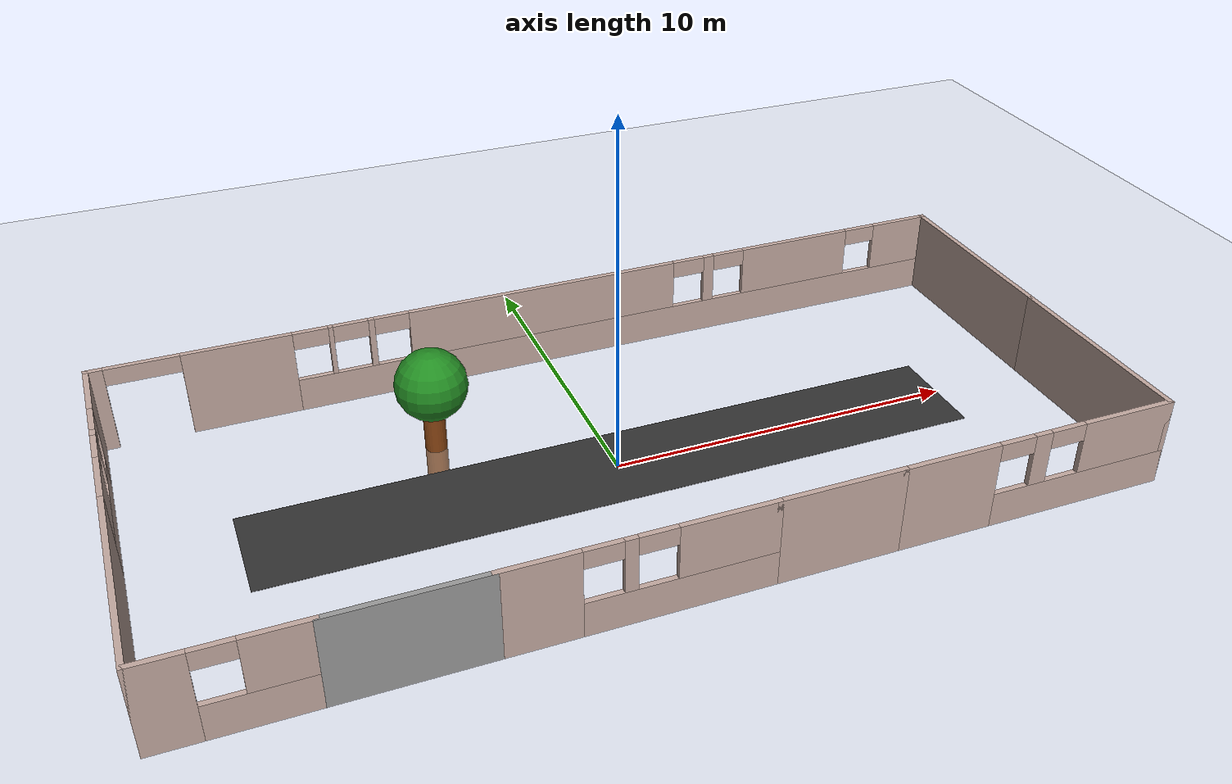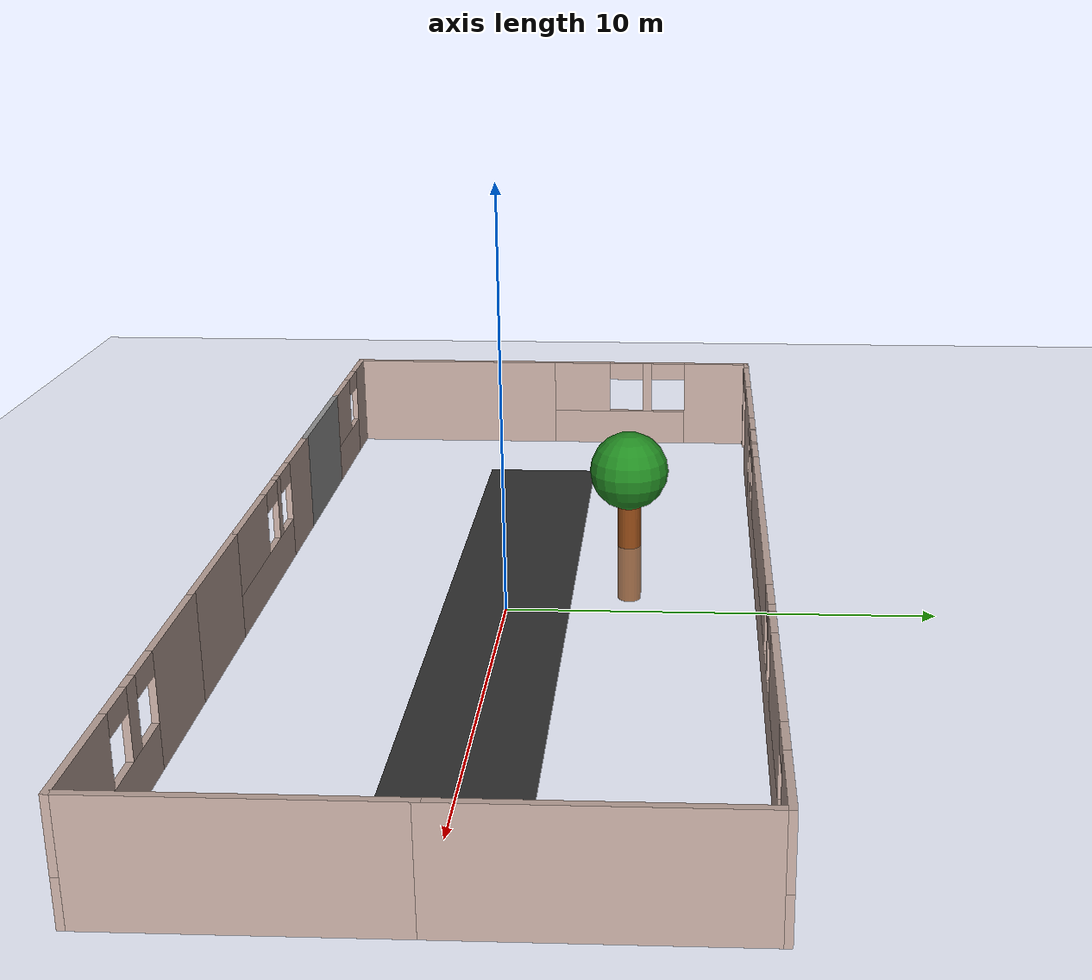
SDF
<sdf version="1.7">
 <world name="default">
  <plugin name="hello" filename="libhello.so"/>
  <light name="sun" type="directional">
   <pose>0 0 10 0 -0 0</pose>
   <diffuse>0.8 0.8 0.8 1</diffuse>
   <specular>0.1 0.1 0.1 1</specular>
   <attenuation>
    <range>1000</range>
    <constant>0.9</constant>
    <linear>0.01</linear>
    <quadratic>0.001</quadratic>
   </attenuation>
   <direction>-0.5 0.5 -1</direction>
   <spot><inner_angle>0</inner_angle><outer_angle>0</outer_angle><falloff>0</falloff></spot>
  </light>
  <model name="ground_plane">
   <static>1</static>
   <link name="link">
    <collision name="collision">
     <geometry><plane><normal>0 0 1</normal><size>100 100</size></plane></geometry>
     <surface><friction><ode><mu>100</mu><mu2>50</mu2></ode></friction></surface>
    </collision>
    <visual name="visual">
     <cast_shadows>0</cast_shadows>
     <geometry><plane><normal>0 0 1</normal><size>100 100</size></plane></geometry>
     <material>
      <script><uri>file://media/materials/scripts/gazebo.material</uri><name>Gazebo/Grey</name></script>
     </material>
    </visual>
   </link>
  </model>
  <gravity>0 0 -9.8</gravity>
  <magnetic_field>6e-06 2.3e-05 -4.2e-05</magnetic_field>
  <atmosphere type="adiabatic"/>
  <physics name="default_physics" default="0" type="ode">
   <max_step_size>0.001</max_step_size>
   <real_time_factor>1</real_time_factor>
   <real_time_update_rate>1000</real_time_update_rate>
  </physics>
  <scene><ambient>0.4 0.4 0.4 1</ambient><background>0.7 0.7 0.7 1</background><shadows>1</shadows></scene>
  <spherical_coordinates>
   <surface_model>EARTH_WGS84</surface_model>
   <latitude_deg>0</latitude_deg>
   <longitude_deg>0</longitude_deg>
   <elevation>0</elevation>
   <heading_deg>0</heading_deg>
  </spherical_coordinates>
  <model name="Boundary">
   <link name="Wall_0">
    <pose>-12.8748 2.91767 0 0 0 -1.5708</pose>
    <visual name="Wall_0_Visual_0">
     <pose>-2.03434 0 1.25 0 -0 0</pose>
     <geometry><box><size>1.93132 0.15 2.5</size></box></geometry>
     <material>
      <script><uri>file://media/materials/scripts/gazebo.material</uri><name>Gazebo/Grey</name></script>
      <ambient>0.760784 0.662745 0.627451 1</ambient>
      <shader type="pixel"/>
     </material>
    </visual>
    <visual name="Wall_0_Visual_1">
     <pose>0.965658 0 0.5 0 -0 0</pose>
     <geometry><box><size>4.06868 0.15 1</size></box></geometry>
     <material>
      <script><uri>file://media/materials/scripts/gazebo.material</uri><name>Gazebo/Grey</name></script>
      <ambient>0.760784 0.662745 0.627451 1</ambient>
      <shader type="pixel"/>
     </material>
    </visual>
    <visual name="Wall_0_Visual_2">
     <pose>0.061576 0 1.75 0 -0 0</pose>
     <geometry><box><size>0.26052 0.15 1.5</size></box></geometry>
     <material>
      <script><uri>file://media/materials/scripts/gazebo.material</uri><name>Gazebo/Grey</name></script>
      <ambient>0.760784 0.662745 0.627451 1</ambient>
      <shader type="pixel"/>
     </material>
    </visual>
    <visual name="Wall_0_Visual_3">
     <pose>2.09592 0 1.75 0 -0 0</pose>
     <geometry><box><size>1.80816 0.15 1.5</size></box></geometry>
     <material>
      <script><uri>file://media/materials/scripts/gazebo.material</uri><name>Gazebo/Grey</name></script>
      <ambient>0.760784 0.662745 0.627451 1</ambient>
      <shader type="pixel"/>
     </material>
    </visual>
    <visual name="Wall_0_Visual_4">
     <pose>-0.568684 0 2.25 0 -0 0</pose>
     <geometry><box><size>1 0.15 0.5</size></box></geometry>
     <material>
      <script><uri>file://media/materials/scripts/gazebo.material</uri><name>Gazebo/Grey</name></script>
      <ambient>0.760784 0.662745 0.627451 1</ambient>
      <shader type="pixel"/>
     </material>
    </visual>
    <visual name="Wall_0_Visual_5">
     <pose>0.691837 0 2.25 0 -0 0</pose>
     <geometry><box><size>1 0.15 0.5</size></box></geometry>
     <material>
      <script><uri>file://media/materials/scripts/gazebo.material</uri><name>Gazebo/Grey</name></script>
      <ambient>0.760784 0.662745 0.627451 1</ambient>
      <shader type="pixel"/>
     </material>
    </visual>
    <collision name="Wall_0_Collision_0">
     <pose>-2.03434 0 1.25 0 -0 0</pose>
     <geometry><box><size>1.93132 0.15 2.5</size></box></geometry>
     <surface>
      <friction>
       <ode><mu>1</mu><mu2>1</mu2><fdir1>0 0 0</fdir1><slip1>0</slip1><slip2>0</slip2></ode>
       <torsional>
        <coefficient>1</coefficient>
        <patch_radius>0</patch_radius>
        <surface_radius>0</surface_radius>
        <use_patch_radius>1</use_patch_radius>
        <ode><slip>0</slip></ode>
       </torsional>
      </friction>
      <bounce><restitution_coefficient>0</restitution_coefficient><threshold>1e+06</threshold></bounce>
      <contact>
       <collide_without_contact>0</collide_without_contact>
       <collide_without_contact_bitmask>1</collide_without_contact_bitmask>
       <collide_bitmask>1</collide_bitmask>
       <ode>
        <soft_cfm>0</soft_cfm>
        <soft_erp>0.2</soft_erp>
        <kp>1e+13</kp>
        <kd>1</kd>
        <max_vel>0.01</max_vel>
        <min_depth>0</min_depth>
       </ode>
       <bullet>
        <split_impulse>1</split_impulse>
        <split_impulse_penetration_threshold>-0.01</split_impulse_penetration_threshold>
        <soft_cfm>0</soft_cfm>
        <soft_erp>0.2</soft_erp>
        <kp>1e+13</kp>
        <kd>1</kd>
       </bullet>
      </contact>
     </surface>
    </collision>
    <collision name="Wall_0_Collision_1">
     <pose>0.965658 0 0.5 0 -0 0</pose>
     <geometry><box><size>4.06868 0.15 1</size></box></geometry>
     <surface>
      <friction>
       <ode><mu>1</mu><mu2>1</mu2><fdir1>0 0 0</fdir1><slip1>0</slip1><slip2>0</slip2></ode>
       <torsional>
        <coefficient>1</coefficient>
        <patch_radius>0</patch_radius>
        <surface_radius>0</surface_radius>
        <use_patch_radius>1</use_patch_radius>
        <ode><slip>0</slip></ode>
       </torsional>
      </friction>
      <bounce><restitution_coefficient>0</restitution_coefficient><threshold>1e+06</threshold></bounce>
      <contact>
       <collide_without_contact>0</collide_without_contact>
       <collide_without_contact_bitmask>1</collide_without_contact_bitmask>
       <collide_bitmask>1</collide_bitmask>
       <ode>
        <soft_cfm>0</soft_cfm>
        <soft_erp>0.2</soft_erp>
        <kp>1e+13</kp>
        <kd>1</kd>
        <max_vel>0.01</max_vel>
        <min_depth>0</min_depth>
       </ode>
       <bullet>
        <split_impulse>1</split_impulse>
        <split_impulse_penetration_threshold>-0.01</split_impulse_penetration_threshold>
        <soft_cfm>0</soft_cfm>
        <soft_erp>0.2</soft_erp>
        <kp>1e+13</kp>
        <kd>1</kd>
       </bullet>
      </contact>
     </surface>
    </collision>
    <collision name="Wall_0_Collision_2">
     <pose>0.061576 0 1.75 0 -0 0</pose>
     <geometry><box><size>0.26052 0.15 1.5</size></box></geometry>
     <surface>
      <friction>
       <ode><mu>1</mu><mu2>1</mu2><fdir1>0 0 0</fdir1><slip1>0</slip1><slip2>0</slip2></ode>
       <torsional>
        <coefficient>1</coefficient>
        <patch_radius>0</patch_radius>
        <surface_radius>0</surface_radius>
        <use_patch_radius>1</use_patch_radius>
        <ode><slip>0</slip></ode>
       </torsional>
      </friction>
      <bounce><restitution_coefficient>0</restitution_coefficient><threshold>1e+06</threshold></bounce>
      <contact>
       <collide_without_contact>0</collide_without_contact>
       <collide_without_contact_bitmask>1</collide_without_contact_bitmask>
       <collide_bitmask>1</collide_bitmask>
       <ode>
        <soft_cfm>0</soft_cfm>
        <soft_erp>0.2</soft_erp>
        <kp>1e+13</kp>
        <kd>1</kd>
        <max_vel>0.01</max_vel>
        <min_depth>0</min_depth>
       </ode>
       <bullet>
        <split_impulse>1</split_impulse>
        <split_impulse_penetration_threshold>-0.01</split_impulse_penetration_threshold>
        <soft_cfm>0</soft_cfm>
        <soft_erp>0.2</soft_erp>
        <kp>1e+13</kp>
        <kd>1</kd>
       </bullet>
      </contact>
     </surface>
    </collision>
    <collision name="Wall_0_Collision_3">
     <pose>2.09592 0 1.75 0 -0 0</pose>
     <geometry><box><size>1.80816 0.15 1.5</size></box></geometry>
     <surface>
      <friction>
       <ode><mu>1</mu><mu2>1</mu2><fdir1>0 0 0</fdir1><slip1>0</slip1><slip2>0</slip2></ode>
       <torsional>
        <coefficient>1</coefficient>
        <patch_radius>0</patch_radius>
        <surface_radius>0</surface_radius>
        <use_patch_radius>1</use_patch_radius>
        <ode><slip>0</slip></ode>
       </torsional>
      </friction>
      <bounce><restitution_coefficient>0</restitution_coefficient><threshold>1e+06</threshold></bounce>
      <contact>
       <collide_without_contact>0</collide_without_contact>
       <collide_without_contact_bitmask>1</collide_without_contact_bitmask>
       <collide_bitmask>1</collide_bitmask>
       <ode>
        <soft_cfm>0</soft_cfm>
        <soft_erp>0.2</soft_erp>
        <kp>1e+13</kp>
        <kd>1</kd>
        <max_vel>0.01</max_vel>
        <min_depth>0</min_depth>
       </ode>
       <bullet>
        <split_impulse>1</split_impulse>
        <split_impulse_penetration_threshold>-0.01</split_impulse_penetration_threshold>
        <soft_cfm>0</soft_cfm>
        <soft_erp>0.2</soft_erp>
        <kp>1e+13</kp>
        <kd>1</kd>
       </bullet>
      </contact>
     </surface>
    </collision>
    <collision name="Wall_0_Collision_4">
     <pose>-0.568684 0 2.25 0 -0 0</pose>
     <geometry><box><size>1 0.15 0.5</size></box></geometry>
     <surface>
      <friction>
       <ode><mu>1</mu><mu2>1</mu2><fdir1>0 0 0</fdir1><slip1>0</slip1><slip2>0</slip2></ode>
       <torsional>
        <coefficient>1</coefficient>
        <patch_radius>0</patch_radius>
        <surface_radius>0</surface_radius>
        <use_patch_radius>1</use_patch_radius>
        <ode><slip>0</slip></ode>
       </torsional>
      </friction>
      <bounce><restitution_coefficient>0</restitution_coefficient><threshold>1e+06</threshold></bounce>
      <contact>
       <collide_without_contact>0</collide_without_contact>
       <collide_without_contact_bitmask>1</collide_without_contact_bitmask>
       <collide_bitmask>1</collide_bitmask>
       <ode>
        <soft_cfm>0</soft_cfm>
        <soft_erp>0.2</soft_erp>
        <kp>1e+13</kp>
        <kd>1</kd>
        <max_vel>0.01</max_vel>
        <min_depth>0</min_depth>
       </ode>
       <bullet>
        <split_impulse>1</split_impulse>
        <split_impulse_penetration_threshold>-0.01</split_impulse_penetration_threshold>
        <soft_cfm>0</soft_cfm>
        <soft_erp>0.2</soft_erp>
        <kp>1e+13</kp>
        <kd>1</kd>
       </bullet>
      </contact>
     </surface>
    </collision>
    <collision name="Wall_0_Collision_5">
     <pose>0.691837 0 2.25 0 -0 0</pose>
     <geometry><box><size>1 0.15 0.5</size></box></geometry>
     <surface>
      <friction>
       <ode><mu>1</mu><mu2>1</mu2><fdir1>0 0 0</fdir1><slip1>0</slip1><slip2>0</slip2></ode>
       <torsional>
        <coefficient>1</coefficient>
        <patch_radius>0</patch_radius>
        <surface_radius>0</surface_radius>
        <use_patch_radius>1</use_patch_radius>
        <ode><slip>0</slip></ode>
       </torsional>
      </friction>
      <bounce><restitution_coefficient>0</restitution_coefficient><threshold>1e+06</threshold></bounce>
      <contact>
       <collide_without_contact>0</collide_without_contact>
       <collide_without_contact_bitmask>1</collide_without_contact_bitmask>
       <collide_bitmask>1</collide_bitmask>
       <ode>
        <soft_cfm>0</soft_cfm>
        <soft_erp>0.2</soft_erp>
        <kp>1e+13</kp>
        <kd>1</kd>
        <max_vel>0.01</max_vel>
        <min_depth>0</min_depth>
       </ode>
       <bullet>
        <split_impulse>1</split_impulse>
        <split_impulse_penetration_threshold>-0.01</split_impulse_penetration_threshold>
        <soft_cfm>0</soft_cfm>
        <soft_erp>0.2</soft_erp>
        <kp>1e+13</kp>
        <kd>1</kd>
       </bullet>
      </contact>
     </surface>
    </collision>
   </link>
   <link name="Wall_10">
    <pose>-7.1 -5.85736 0 0 0 -1.2e-05</pose>
    <visual name="Wall_10_Visual">
     <pose>0 0 1.25 0 -0 0</pose>
     <geometry><box><size>4 0.15 2.5</size></box></geometry>
     <material>
      <script><uri>file://media/materials/scripts/gazebo.material</uri><name>Gazebo/Grey</name></script>
      <ambient>1 1 1 1</ambient>
      <shader type="pixel"/>
     </material>
    </visual>
    <collision name="Wall_10_Collision">
     <pose>0 0 1.25 0 -0 0</pose>
     <geometry><box><size>4 0.15 2.5</size></box></geometry>
     <surface>
      <friction>
       <ode><mu>1</mu><mu2>1</mu2><fdir1>0 0 0</fdir1><slip1>0</slip1><slip2>0</slip2></ode>
       <torsional>
        <coefficient>1</coefficient>
        <patch_radius>0</patch_radius>
        <surface_radius>0</surface_radius>
        <use_patch_radius>1</use_patch_radius>
        <ode><slip>0</slip></ode>
       </torsional>
      </friction>
      <bounce><restitution_coefficient>0</restitution_coefficient><threshold>1e+06</threshold></bounce>
      <contact>
       <collide_without_contact>0</collide_without_contact>
       <collide_without_contact_bitmask>1</collide_without_contact_bitmask>
       <collide_bitmask>1</collide_bitmask>
       <ode>
        <soft_cfm>0</soft_cfm>
        <soft_erp>0.2</soft_erp>
        <kp>1e+13</kp>
        <kd>1</kd>
        <max_vel>0.01</max_vel>
        <min_depth>0</min_depth>
       </ode>
       <bullet>
        <split_impulse>1</split_impulse>
        <split_impulse_penetration_threshold>-0.01</split_impulse_penetration_threshold>
        <soft_cfm>0</soft_cfm>
        <soft_erp>0.2</soft_erp>
        <kp>1e+13</kp>
        <kd>1</kd>
       </bullet>
      </contact>
     </surface>
    </collision>
   </link>
   <link name="Wall_14">
    <pose>-1.75018 -5.85738 0 0 -0 0</pose>
    <visual name="Wall_14_Visual_0">
     <pose>-2.46755 0 1.25 0 -0 0</pose>
     <geometry><box><size>2.0649 0.15 2.5</size></box></geometry>
     <material>
      <script><uri>file://media/materials/scripts/gazebo.material</uri><name>Gazebo/Grey</name></script>
      <ambient>0.760784 0.662745 0.627451 1</ambient>
      <shader type="pixel"/>
     </material>
    </visual>
    <visual name="Wall_14_Visual_1">
     <pose>1.03245 0 0.5 0 -0 0</pose>
     <geometry><box><size>4.93509 0.15 1</size></box></geometry>
     <material>
      <script><uri>file://media/materials/scripts/gazebo.material</uri><name>Gazebo/Grey</name></script>
      <ambient>0.760784 0.662745 0.627451 1</ambient>
      <shader type="pixel"/>
     </material>
    </visual>
    <visual name="Wall_14_Visual_2">
     <pose>-0.267578 0 1.75 0 -0 0</pose>
     <geometry><box><size>0.335034 0.15 1.5</size></box></geometry>
     <material>
      <script><uri>file://media/materials/scripts/gazebo.material</uri><name>Gazebo/Grey</name></script>
      <ambient>0.760784 0.662745 0.627451 1</ambient>
      <shader type="pixel"/>
     </material>
    </visual>
    <visual name="Wall_14_Visual_3">
     <pose>2.19997 0 1.75 0 -0 0</pose>
     <geometry><box><size>2.60006 0.15 1.5</size></box></geometry>
     <material>
      <script><uri>file://media/materials/scripts/gazebo.material</uri><name>Gazebo/Grey</name></script>
      <ambient>0.760784 0.662745 0.627451 1</ambient>
      <shader type="pixel"/>
     </material>
    </visual>
    <visual name="Wall_14_Visual_4">
     <pose>-0.935095 0 2.25 0 -0 0</pose>
     <geometry><box><size>1 0.15 0.5</size></box></geometry>
     <material>
      <script><uri>file://media/materials/scripts/gazebo.material</uri><name>Gazebo/Grey</name></script>
      <ambient>0.760784 0.662745 0.627451 1</ambient>
      <shader type="pixel"/>
     </material>
    </visual>
    <visual name="Wall_14_Visual_5">
     <pose>0.399939 0 2.25 0 -0 0</pose>
     <geometry><box><size>1 0.15 0.5</size></box></geometry>
     <material>
      <script><uri>file://media/materials/scripts/gazebo.material</uri><name>Gazebo/Grey</name></script>
      <ambient>0.760784 0.662745 0.627451 1</ambient>
      <shader type="pixel"/>
     </material>
    </visual>
    <collision name="Wall_14_Collision_0">
     <pose>-2.46755 0 1.25 0 -0 0</pose>
     <geometry><box><size>2.0649 0.15 2.5</size></box></geometry>
     <surface>
      <friction>
       <ode><mu>1</mu><mu2>1</mu2><fdir1>0 0 0</fdir1><slip1>0</slip1><slip2>0</slip2></ode>
       <torsional>
        <coefficient>1</coefficient>
        <patch_radius>0</patch_radius>
        <surface_radius>0</surface_radius>
        <use_patch_radius>1</use_patch_radius>
        <ode><slip>0</slip></ode>
       </torsional>
      </friction>
      <bounce><restitution_coefficient>0</restitution_coefficient><threshold>1e+06</threshold></bounce>
      <contact>
       <collide_without_contact>0</collide_without_contact>
       <collide_without_contact_bitmask>1</collide_without_contact_bitmask>
       <collide_bitmask>1</collide_bitmask>
       <ode>
        <soft_cfm>0</soft_cfm>
        <soft_erp>0.2</soft_erp>
        <kp>1e+13</kp>
        <kd>1</kd>
        <max_vel>0.01</max_vel>
        <min_depth>0</min_depth>
       </ode>
       <bullet>
        <split_impulse>1</split_impulse>
        <split_impulse_penetration_threshold>-0.01</split_impulse_penetration_threshold>
        <soft_cfm>0</soft_cfm>
        <soft_erp>0.2</soft_erp>
        <kp>1e+13</kp>
        <kd>1</kd>
       </bullet>
      </contact>
     </surface>
    </collision>
    <collision name="Wall_14_Collision_1">
     <pose>1.03245 0 0.5 0 -0 0</pose>
     <geometry><box><size>4.93509 0.15 1</size></box></geometry>
     <surface>
      <friction>
       <ode><mu>1</mu><mu2>1</mu2><fdir1>0 0 0</fdir1><slip1>0</slip1><slip2>0</slip2></ode>
       <torsional>
        <coefficient>1</coefficient>
        <patch_radius>0</patch_radius>
        <surface_radius>0</surface_radius>
        <use_patch_radius>1</use_patch_radius>
        <ode><slip>0</slip></ode>
       </torsional>
      </friction>
      <bounce><restitution_coefficient>0</restitution_coefficient><threshold>1e+06</threshold></bounce>
      <contact>
       <collide_without_contact>0</collide_without_contact>
       <collide_without_contact_bitmask>1</collide_without_contact_bitmask>
       <collide_bitmask>1</collide_bitmask>
       <ode>
        <soft_cfm>0</soft_cfm>
        <soft_erp>0.2</soft_erp>
        <kp>1e+13</kp>
        <kd>1</kd>
        <max_vel>0.01</max_vel>
        <min_depth>0</min_depth>
       </ode>
       <bullet>
        <split_impulse>1</split_impulse>
        <split_impulse_penetration_threshold>-0.01</split_impulse_penetration_threshold>
        <soft_cfm>0</soft_cfm>
        <soft_erp>0.2</soft_erp>
        <kp>1e+13</kp>
        <kd>1</kd>
       </bullet>
      </contact>
     </surface>
    </collision>
    <collision name="Wall_14_Collision_3">
     <pose>2.19997 0 1.75 0 -0 0</pose>
     <geometry><box><size>2.60006 0.15 1.5</size></box></geometry>
     <surface>
      <friction>
       <ode><mu>1</mu><mu2>1</mu2><fdir1>0 0 0</fdir1><slip1>0</slip1><slip2>0</slip2></ode>
       <torsional>
        <coefficient>1</coefficient>
        <patch_radius>0</patch_radius>
        <surface_radius>0</surface_radius>
        <use_patch_radius>1</use_patch_radius>
        <ode><slip>0</slip></ode>
       </torsional>
      </friction>
      <bounce><restitution_coefficient>0</restitution_coefficient><threshold>1e+06</threshold></bounce>
      <contact>
       <collide_without_contact>0</collide_without_contact>
       <collide_without_contact_bitmask>1</collide_without_contact_bitmask>
       <collide_bitmask>1</collide_bitmask>
       <ode>
        <soft_cfm>0</soft_cfm>
        <soft_erp>0.2</soft_erp>
        <kp>1e+13</kp>
        <kd>1</kd>
        <max_vel>0.01</max_vel>
        <min_depth>0</min_depth>
       </ode>
       <bullet>
        <split_impulse>1</split_impulse>
        <split_impulse_penetration_threshold>-0.01</split_impulse_penetration_threshold>
        <soft_cfm>0</soft_cfm>
        <soft_erp>0.2</soft_erp>
        <kp>1e+13</kp>
        <kd>1</kd>
       </bullet>
      </contact>
     </surface>
    </collision>
    <collision name="Wall_14_Collision_2">
     <pose>-0.267578 0 1.75 0 -0 0</pose>
     <geometry><box><size>0.335034 0.15 1.5</size></box></geometry>
     <surface>
      <friction>
       <ode><mu>1</mu><mu2>1</mu2><fdir1>0 0 0</fdir1><slip1>0</slip1><slip2>0</slip2></ode>
       <torsional>
        <coefficient>1</coefficient>
        <patch_radius>0</patch_radius>
        <surface_radius>0</surface_radius>
        <use_patch_radius>1</use_patch_radius>
        <ode><slip>0</slip></ode>
       </torsional>
      </friction>
      <bounce><restitution_coefficient>0</restitution_coefficient><threshold>1e+06</threshold></bounce>
      <contact>
       <collide_without_contact>0</collide_without_contact>
       <collide_without_contact_bitmask>1</collide_without_contact_bitmask>
       <collide_bitmask>1</collide_bitmask>
       <ode>
        <soft_cfm>0</soft_cfm>
        <soft_erp>0.2</soft_erp>
        <kp>1e+13</kp>
        <kd>1</kd>
        <max_vel>0.01</max_vel>
        <min_depth>0</min_depth>
       </ode>
       <bullet>
        <split_impulse>1</split_impulse>
        <split_impulse_penetration_threshold>-0.01</split_impulse_penetration_threshold>
        <soft_cfm>0</soft_cfm>
        <soft_erp>0.2</soft_erp>
        <kp>1e+13</kp>
        <kd>1</kd>
       </bullet>
      </contact>
     </surface>
    </collision>
    <collision name="Wall_14_Collision_4">
     <pose>-0.935095 0 2.25 0 -0 0</pose>
     <geometry><box><size>1 0.15 0.5</size></box></geometry>
     <surface>
      <friction>
       <ode><mu>1</mu><mu2>1</mu2><fdir1>0 0 0</fdir1><slip1>0</slip1><slip2>0</slip2></ode>
       <torsional>
        <coefficient>1</coefficient>
        <patch_radius>0</patch_radius>
        <surface_radius>0</surface_radius>
        <use_patch_radius>1</use_patch_radius>
        <ode><slip>0</slip></ode>
       </torsional>
      </friction>
      <bounce><restitution_coefficient>0</restitution_coefficient><threshold>1e+06</threshold></bounce>
      <contact>
       <collide_without_contact>0</collide_without_contact>
       <collide_without_contact_bitmask>1</collide_without_contact_bitmask>
       <collide_bitmask>1</collide_bitmask>
       <ode>
        <soft_cfm>0</soft_cfm>
        <soft_erp>0.2</soft_erp>
        <kp>1e+13</kp>
        <kd>1</kd>
        <max_vel>0.01</max_vel>
        <min_depth>0</min_depth>
       </ode>
       <bullet>
        <split_impulse>1</split_impulse>
        <split_impulse_penetration_threshold>-0.01</split_impulse_penetration_threshold>
        <soft_cfm>0</soft_cfm>
        <soft_erp>0.2</soft_erp>
        <kp>1e+13</kp>
        <kd>1</kd>
       </bullet>
      </contact>
     </surface>
    </collision>
    <collision name="Wall_14_Collision_5">
     <pose>0.399939 0 2.25 0 -0 0</pose>
     <geometry><box><size>1 0.15 0.5</size></box></geometry>
     <surface>
      <friction>
       <ode><mu>1</mu><mu2>1</mu2><fdir1>0 0 0</fdir1><slip1>0</slip1><slip2>0</slip2></ode>
       <torsional>
        <coefficient>1</coefficient>
        <patch_radius>0</patch_radius>
        <surface_radius>0</surface_radius>
        <use_patch_radius>1</use_patch_radius>
        <ode><slip>0</slip></ode>
       </torsional>
      </friction>
      <bounce><restitution_coefficient>0</restitution_coefficient><threshold>1e+06</threshold></bounce>
      <contact>
       <collide_without_contact>0</collide_without_contact>
       <collide_without_contact_bitmask>1</collide_without_contact_bitmask>
       <collide_bitmask>1</collide_bitmask>
       <ode>
        <soft_cfm>0</soft_cfm>
        <soft_erp>0.2</soft_erp>
        <kp>1e+13</kp>
        <kd>1</kd>
        <max_vel>0.01</max_vel>
        <min_depth>0</min_depth>
       </ode>
       <bullet>
        <split_impulse>1</split_impulse>
        <split_impulse_penetration_threshold>-0.01</split_impulse_penetration_threshold>
        <soft_cfm>0</soft_cfm>
        <soft_erp>0.2</soft_erp>
        <kp>1e+13</kp>
        <kd>1</kd>
       </bullet>
      </contact>
     </surface>
    </collision>
   </link>
   <link name="Wall_2">
    <pose>-12.8748 -2.93233 0 0 0 -1.5708</pose>
    <visual name="Wall_2_Visual">
     <pose>0 0 1.25 0 -0 0</pose>
     <geometry><box><size>6 0.15 2.5</size></box></geometry>
     <material>
      <script><uri>file://media/materials/scripts/gazebo.material</uri><name>Gazebo/Grey</name></script>
      <ambient>0.760784 0.662745 0.627451 1</ambient>
      <shader type="pixel"/>
     </material>
    </visual>
    <collision name="Wall_2_Collision">
     <pose>0 0 1.25 0 -0 0</pose>
     <geometry><box><size>6 0.15 2.5</size></box></geometry>
     <surface>
      <friction>
       <ode><mu>1</mu><mu2>1</mu2><fdir1>0 0 0</fdir1><slip1>0</slip1><slip2>0</slip2></ode>
       <torsional>
        <coefficient>1</coefficient>
        <patch_radius>0</patch_radius>
        <surface_radius>0</surface_radius>
        <use_patch_radius>1</use_patch_radius>
        <ode><slip>0</slip></ode>
       </torsional>
      </friction>
      <bounce><restitution_coefficient>0</restitution_coefficient><threshold>1e+06</threshold></bounce>
      <contact>
       <collide_without_contact>0</collide_without_contact>
       <collide_without_contact_bitmask>1</collide_without_contact_bitmask>
       <collide_bitmask>1</collide_bitmask>
       <ode>
        <soft_cfm>0</soft_cfm>
        <soft_erp>0.2</soft_erp>
        <kp>1e+13</kp>
        <kd>1</kd>
        <max_vel>0.01</max_vel>
        <min_depth>0</min_depth>
       </ode>
       <bullet>
        <split_impulse>1</split_impulse>
        <split_impulse_penetration_threshold>-0.01</split_impulse_penetration_threshold>
        <soft_cfm>0</soft_cfm>
        <soft_erp>0.2</soft_erp>
        <kp>1e+13</kp>
        <kd>1</kd>
       </bullet>
      </contact>
     </surface>
    </collision>
   </link>
   <link name="Wall_23">
    <pose>3.34982 -5.85738 0 0 -0 0</pose>
    <visual name="Wall_23_Visual">
     <pose>0 0 1.25 0 -0 0</pose>
     <geometry><box><size>3.5 0.15 2.5</size></box></geometry>
     <material>
      <script><uri>file://media/materials/scripts/gazebo.material</uri><name>Gazebo/Grey</name></script>
      <ambient>0.760784 0.662745 0.627451 1</ambient>
      <shader type="pixel"/>
     </material>
    </visual>
    <collision name="Wall_23_Collision">
     <pose>0 0 1.25 0 -0 0</pose>
     <geometry><box><size>3.5 0.15 2.5</size></box></geometry>
     <surface>
      <friction>
       <ode><mu>1</mu><mu2>1</mu2><fdir1>0 0 0</fdir1><slip1>0</slip1><slip2>0</slip2></ode>
       <torsional>
        <coefficient>1</coefficient>
        <patch_radius>0</patch_radius>
        <surface_radius>0</surface_radius>
        <use_patch_radius>1</use_patch_radius>
        <ode><slip>0</slip></ode>
       </torsional>
      </friction>
      <bounce><restitution_coefficient>0</restitution_coefficient><threshold>1e+06</threshold></bounce>
      <contact>
       <collide_without_contact>0</collide_without_contact>
       <collide_without_contact_bitmask>1</collide_without_contact_bitmask>
       <collide_bitmask>1</collide_bitmask>
       <ode>
        <soft_cfm>0</soft_cfm>
        <soft_erp>0.2</soft_erp>
        <kp>1e+13</kp>
        <kd>1</kd>
        <max_vel>0.01</max_vel>
        <min_depth>0</min_depth>
       </ode>
       <bullet>
        <split_impulse>1</split_impulse>
        <split_impulse_penetration_threshold>-0.01</split_impulse_penetration_threshold>
        <soft_cfm>0</soft_cfm>
        <soft_erp>0.2</soft_erp>
        <kp>1e+13</kp>
        <kd>1</kd>
       </bullet>
      </contact>
     </surface>
    </collision>
   </link>
   <link name="Wall_29">
    <pose>8.94982 -5.85738 0 0 -0 0</pose>
    <visual name="Wall_29_Visual_0">
     <pose>-2.60604 0 1.25 0 -0 0</pose>
     <geometry><box><size>2.78791 0.15 2.5</size></box></geometry>
     <material>
      <script><uri>file://media/materials/scripts/gazebo.material</uri><name>Gazebo/Grey</name></script>
      <ambient>0.760784 0.662745 0.627451 1</ambient>
      <shader type="pixel"/>
     </material>
    </visual>
    <visual name="Wall_29_Visual_1">
     <pose>1.39396 0 0.5 0 -0 0</pose>
     <geometry><box><size>5.21209 0.15 1</size></box></geometry>
     <material>
      <script><uri>file://media/materials/scripts/gazebo.material</uri><name>Gazebo/Grey</name></script>
      <ambient>0.760784 0.662745 0.627451 1</ambient>
      <shader type="pixel"/>
     </material>
    </visual>
    <visual name="Wall_29_Visual_2">
     <pose>0.036339 0 1.75 0 -0 0</pose>
     <geometry><box><size>0.496857 0.15 1.5</size></box></geometry>
     <material>
      <script><uri>file://media/materials/scripts/gazebo.material</uri><name>Gazebo/Grey</name></script>
      <ambient>0.760784 0.662745 0.627451 1</ambient>
      <shader type="pixel"/>
     </material>
    </visual>
    <visual name="Wall_29_Visual_3">
     <pose>2.64238 0 1.75 0 -0 0</pose>
     <geometry><box><size>2.71523 0.15 1.5</size></box></geometry>
     <material>
      <script><uri>file://media/materials/scripts/gazebo.material</uri><name>Gazebo/Grey</name></script>
      <ambient>0.760784 0.662745 0.627451 1</ambient>
      <shader type="pixel"/>
     </material>
    </visual>
    <visual name="Wall_29_Visual_4">
     <pose>-0.71209 0 2.25 0 -0 0</pose>
     <geometry><box><size>1 0.15 0.5</size></box></geometry>
     <material>
      <script><uri>file://media/materials/scripts/gazebo.material</uri><name>Gazebo/Grey</name></script>
      <ambient>0.760784 0.662745 0.627451 1</ambient>
      <shader type="pixel"/>
     </material>
    </visual>
    <visual name="Wall_29_Visual_5">
     <pose>0.784767 0 2.25 0 -0 0</pose>
     <geometry><box><size>1 0.15 0.5</size></box></geometry>
     <material>
      <script><uri>file://media/materials/scripts/gazebo.material</uri><name>Gazebo/Grey</name></script>
      <ambient>0.760784 0.662745 0.627451 1</ambient>
      <shader type="pixel"/>
     </material>
    </visual>
    <collision name="Wall_29_Collision_0">
     <pose>-2.60604 0 1.25 0 -0 0</pose>
     <geometry><box><size>2.78791 0.15 2.5</size></box></geometry>
     <surface>
      <friction>
       <ode><mu>1</mu><mu2>1</mu2><fdir1>0 0 0</fdir1><slip1>0</slip1><slip2>0</slip2></ode>
       <torsional>
        <coefficient>1</coefficient>
        <patch_radius>0</patch_radius>
        <surface_radius>0</surface_radius>
        <use_patch_radius>1</use_patch_radius>
        <ode><slip>0</slip></ode>
       </torsional>
      </friction>
      <bounce><restitution_coefficient>0</restitution_coefficient><threshold>1e+06</threshold></bounce>
      <contact>
       <collide_without_contact>0</collide_without_contact>
       <collide_without_contact_bitmask>1</collide_without_contact_bitmask>
       <collide_bitmask>1</collide_bitmask>
       <ode>
        <soft_cfm>0</soft_cfm>
        <soft_erp>0.2</soft_erp>
        <kp>1e+13</kp>
        <kd>1</kd>
        <max_vel>0.01</max_vel>
        <min_depth>0</min_depth>
       </ode>
       <bullet>
        <split_impulse>1</split_impulse>
        <split_impulse_penetration_threshold>-0.01</split_impulse_penetration_threshold>
        <soft_cfm>0</soft_cfm>
        <soft_erp>0.2</soft_erp>
        <kp>1e+13</kp>
        <kd>1</kd>
       </bullet>
      </contact>
     </surface>
    </collision>
    <collision name="Wall_29_Collision_1">
     <pose>1.39396 0 0.5 0 -0 0</pose>
     <geometry><box><size>5.21209 0.15 1</size></box></geometry>
     <surface>
      <friction>
       <ode><mu>1</mu><mu2>1</mu2><fdir1>0 0 0</fdir1><slip1>0</slip1><slip2>0</slip2></ode>
       <torsional>
        <coefficient>1</coefficient>
        <patch_radius>0</patch_radius>
        <surface_radius>0</surface_radius>
        <use_patch_radius>1</use_patch_radius>
        <ode><slip>0</slip></ode>
       </torsional>
      </friction>
      <bounce><restitution_coefficient>0</restitution_coefficient><threshold>1e+06</threshold></bounce>
      <contact>
       <collide_without_contact>0</collide_without_contact>
       <collide_without_contact_bitmask>1</collide_without_contact_bitmask>
       <collide_bitmask>1</collide_bitmask>
       <ode>
        <soft_cfm>0</soft_cfm>
        <soft_erp>0.2</soft_erp>
        <kp>1e+13</kp>
        <kd>1</kd>
        <max_vel>0.01</max_vel>
        <min_depth>0</min_depth>
       </ode>
       <bullet>
        <split_impulse>1</split_impulse>
        <split_impulse_penetration_threshold>-0.01</split_impulse_penetration_threshold>
        <soft_cfm>0</soft_cfm>
        <soft_erp>0.2</soft_erp>
        <kp>1e+13</kp>
        <kd>1</kd>
       </bullet>
      </contact>
     </surface>
    </collision>
    <collision name="Wall_29_Collision_2">
     <pose>0.036339 0 1.75 0 -0 0</pose>
     <geometry><box><size>0.496857 0.15 1.5</size></box></geometry>
     <surface>
      <friction>
       <ode><mu>1</mu><mu2>1</mu2><fdir1>0 0 0</fdir1><slip1>0</slip1><slip2>0</slip2></ode>
       <torsional>
        <coefficient>1</coefficient>
        <patch_radius>0</patch_radius>
        <surface_radius>0</surface_radius>
        <use_patch_radius>1</use_patch_radius>
        <ode><slip>0</slip></ode>
       </torsional>
      </friction>
      <bounce><restitution_coefficient>0</restitution_coefficient><threshold>1e+06</threshold></bounce>
      <contact>
       <collide_without_contact>0</collide_without_contact>
       <collide_without_contact_bitmask>1</collide_without_contact_bitmask>
       <collide_bitmask>1</collide_bitmask>
       <ode>
        <soft_cfm>0</soft_cfm>
        <soft_erp>0.2</soft_erp>
        <kp>1e+13</kp>
        <kd>1</kd>
        <max_vel>0.01</max_vel>
        <min_depth>0</min_depth>
       </ode>
       <bullet>
        <split_impulse>1</split_impulse>
        <split_impulse_penetration_threshold>-0.01</split_impulse_penetration_threshold>
        <soft_cfm>0</soft_cfm>
        <soft_erp>0.2</soft_erp>
        <kp>1e+13</kp>
        <kd>1</kd>
       </bullet>
      </contact>
     </surface>
    </collision>
    <collision name="Wall_29_Collision_3">
     <pose>2.64238 0 1.75 0 -0 0</pose>
     <geometry><box><size>2.71523 0.15 1.5</size></box></geometry>
     <surface>
      <friction>
       <ode><mu>1</mu><mu2>1</mu2><fdir1>0 0 0</fdir1><slip1>0</slip1><slip2>0</slip2></ode>
       <torsional>
        <coefficient>1</coefficient>
        <patch_radius>0</patch_radius>
        <surface_radius>0</surface_radius>
        <use_patch_radius>1</use_patch_radius>
        <ode><slip>0</slip></ode>
       </torsional>
      </friction>
      <bounce><restitution_coefficient>0</restitution_coefficient><threshold>1e+06</threshold></bounce>
      <contact>
       <collide_without_contact>0</collide_without_contact>
       <collide_without_contact_bitmask>1</collide_without_contact_bitmask>
       <collide_bitmask>1</collide_bitmask>
       <ode>
        <soft_cfm>0</soft_cfm>
        <soft_erp>0.2</soft_erp>
        <kp>1e+13</kp>
        <kd>1</kd>
        <max_vel>0.01</max_vel>
        <min_depth>0</min_depth>
       </ode>
       <bullet>
        <split_impulse>1</split_impulse>
        <split_impulse_penetration_threshold>-0.01</split_impulse_penetration_threshold>
        <soft_cfm>0</soft_cfm>
        <soft_erp>0.2</soft_erp>
        <kp>1e+13</kp>
        <kd>1</kd>
       </bullet>
      </contact>
     </surface>
    </collision>
    <collision name="Wall_29_Collision_5">
     <pose>0.784767 0 2.25 0 -0 0</pose>
     <geometry><box><size>1 0.15 0.5</size></box></geometry>
     <surface>
      <friction>
       <ode><mu>1</mu><mu2>1</mu2><fdir1>0 0 0</fdir1><slip1>0</slip1><slip2>0</slip2></ode>
       <torsional>
        <coefficient>1</coefficient>
        <patch_radius>0</patch_radius>
        <surface_radius>0</surface_radius>
        <use_patch_radius>1</use_patch_radius>
        <ode><slip>0</slip></ode>
       </torsional>
      </friction>
      <bounce><restitution_coefficient>0</restitution_coefficient><threshold>1e+06</threshold></bounce>
      <contact>
       <collide_without_contact>0</collide_without_contact>
       <collide_without_contact_bitmask>1</collide_without_contact_bitmask>
       <collide_bitmask>1</collide_bitmask>
       <ode>
        <soft_cfm>0</soft_cfm>
        <soft_erp>0.2</soft_erp>
        <kp>1e+13</kp>
        <kd>1</kd>
        <max_vel>0.01</max_vel>
        <min_depth>0</min_depth>
       </ode>
       <bullet>
        <split_impulse>1</split_impulse>
        <split_impulse_penetration_threshold>-0.01</split_impulse_penetration_threshold>
        <soft_cfm>0</soft_cfm>
        <soft_erp>0.2</soft_erp>
        <kp>1e+13</kp>
        <kd>1</kd>
       </bullet>
      </contact>
     </surface>
    </collision>
    <collision name="Wall_29_Collision_4">
     <pose>-0.71209 0 2.25 0 -0 0</pose>
     <geometry><box><size>1 0.15 0.5</size></box></geometry>
     <surface>
      <friction>
       <ode><mu>1</mu><mu2>1</mu2><fdir1>0 0 0</fdir1><slip1>0</slip1><slip2>0</slip2></ode>
       <torsional>
        <coefficient>1</coefficient>
        <patch_radius>0</patch_radius>
        <surface_radius>0</surface_radius>
        <use_patch_radius>1</use_patch_radius>
        <ode><slip>0</slip></ode>
       </torsional>
      </friction>
      <bounce><restitution_coefficient>0</restitution_coefficient><threshold>1e+06</threshold></bounce>
      <contact>
       <collide_without_contact>0</collide_without_contact>
       <collide_without_contact_bitmask>1</collide_without_contact_bitmask>
       <collide_bitmask>1</collide_bitmask>
       <ode>
        <soft_cfm>0</soft_cfm>
        <soft_erp>0.2</soft_erp>
        <kp>1e+13</kp>
        <kd>1</kd>
        <max_vel>0.01</max_vel>
        <min_depth>0</min_depth>
       </ode>
       <bullet>
        <split_impulse>1</split_impulse>
        <split_impulse_penetration_threshold>-0.01</split_impulse_penetration_threshold>
        <soft_cfm>0</soft_cfm>
        <soft_erp>0.2</soft_erp>
        <kp>1e+13</kp>
        <kd>1</kd>
       </bullet>
      </contact>
     </surface>
    </collision>
   </link>
   <link name="Wall_31">
    <pose>12.8748 -2.93238 0 0 -0 1.5708</pose>
    <visual name="Wall_31_Visual">
     <pose>0 0 1.25 0 -0 0</pose>
     <geometry><box><size>6 0.15 2.5</size></box></geometry>
     <material>
      <script><uri>file://media/materials/scripts/gazebo.material</uri><name>Gazebo/Grey</name></script>
      <ambient>0.760784 0.662745 0.627451 1</ambient>
      <shader type="pixel"/>
     </material>
    </visual>
    <collision name="Wall_31_Collision">
     <pose>0 0 1.25 0 -0 0</pose>
     <geometry><box><size>6 0.15 2.5</size></box></geometry>
     <surface>
      <friction>
       <ode><mu>1</mu><mu2>1</mu2><fdir1>0 0 0</fdir1><slip1>0</slip1><slip2>0</slip2></ode>
       <torsional>
        <coefficient>1</coefficient>
        <patch_radius>0</patch_radius>
        <surface_radius>0</surface_radius>
        <use_patch_radius>1</use_patch_radius>
        <ode><slip>0</slip></ode>
       </torsional>
      </friction>
      <bounce><restitution_coefficient>0</restitution_coefficient><threshold>1e+06</threshold></bounce>
      <contact>
       <collide_without_contact>0</collide_without_contact>
       <collide_without_contact_bitmask>1</collide_without_contact_bitmask>
       <collide_bitmask>1</collide_bitmask>
       <ode>
        <soft_cfm>0</soft_cfm>
        <soft_erp>0.2</soft_erp>
        <kp>1e+13</kp>
        <kd>1</kd>
        <max_vel>0.01</max_vel>
        <min_depth>0</min_depth>
       </ode>
       <bullet>
        <split_impulse>1</split_impulse>
        <split_impulse_penetration_threshold>-0.01</split_impulse_penetration_threshold>
        <soft_cfm>0</soft_cfm>
        <soft_erp>0.2</soft_erp>
        <kp>1e+13</kp>
        <kd>1</kd>
       </bullet>
      </contact>
     </surface>
    </collision>
   </link>
   <link name="Wall_37">
    <pose>12.8748 2.91762 0 0 -0 1.5708</pose>
    <visual name="Wall_37_Visual">
     <pose>0 0 1.25 0 -0 0</pose>
     <geometry><box><size>6 0.15 2.5</size></box></geometry>
     <material>
      <script><uri>file://media/materials/scripts/gazebo.material</uri><name>Gazebo/Grey</name></script>
      <ambient>0.760784 0.662745 0.627451 1</ambient>
      <shader type="pixel"/>
     </material>
    </visual>
    <collision name="Wall_37_Collision">
     <pose>0 0 1.25 0 -0 0</pose>
     <geometry><box><size>6 0.15 2.5</size></box></geometry>
     <surface>
      <friction>
       <ode><mu>1</mu><mu2>1</mu2><fdir1>0 0 0</fdir1><slip1>0</slip1><slip2>0</slip2></ode>
       <torsional>
        <coefficient>1</coefficient>
        <patch_radius>0</patch_radius>
        <surface_radius>0</surface_radius>
        <use_patch_radius>1</use_patch_radius>
        <ode><slip>0</slip></ode>
       </torsional>
      </friction>
      <bounce><restitution_coefficient>0</restitution_coefficient><threshold>1e+06</threshold></bounce>
      <contact>
       <collide_without_contact>0</collide_without_contact>
       <collide_without_contact_bitmask>1</collide_without_contact_bitmask>
       <collide_bitmask>1</collide_bitmask>
       <ode>
        <soft_cfm>0</soft_cfm>
        <soft_erp>0.2</soft_erp>
        <kp>1e+13</kp>
        <kd>1</kd>
        <max_vel>0.01</max_vel>
        <min_depth>0</min_depth>
       </ode>
       <bullet>
        <split_impulse>1</split_impulse>
        <split_impulse_penetration_threshold>-0.01</split_impulse_penetration_threshold>
        <soft_cfm>0</soft_cfm>
        <soft_erp>0.2</soft_erp>
        <kp>1e+13</kp>
        <kd>1</kd>
       </bullet>
      </contact>
     </surface>
    </collision>
   </link>
   <link name="Wall_39">
    <pose>0 5.84264 0 0 0 -2e-06</pose>
    <visual name="Wall_39_Visual_0">
     <pose>-12.6963 0 1.25 0 -0 0</pose>
     <geometry><box><size>0.507003 0.15 2.5</size></box></geometry>
     <material>
      <script><uri>file://media/materials/scripts/gazebo.material</uri><name>Gazebo/Grey</name></script>
      <ambient>0.760784 0.662745 0.627451 1</ambient>
      <shader type="pixel"/>
     </material>
    </visual>
    <visual name="Wall_39_Visual_1">
     <pose>-8.93538 0 1.25 0 -0 0</pose>
     <geometry><box><size>3.01488 0.15 2.5</size></box></geometry>
     <material>
      <script><uri>file://media/materials/scripts/gazebo.material</uri><name>Gazebo/Grey</name></script>
      <ambient>0.760784 0.662745 0.627451 1</ambient>
      <shader type="pixel"/>
     </material>
    </visual>
    <visual name="Wall_39_Visual_2">
     <pose>2.76094 0 0.5 0 -0 0</pose>
     <geometry><box><size>20.3778 0.15 1</size></box></geometry>
     <material>
      <script><uri>file://media/materials/scripts/gazebo.material</uri><name>Gazebo/Grey</name></script>
      <ambient>0.760784 0.662745 0.627451 1</ambient>
      <shader type="pixel"/>
     </material>
    </visual>
    <visual name="Wall_39_Visual_3">
     <pose>-6.3614 0 1.75 0 -0 0</pose>
     <geometry><box><size>0.133081 0.15 1.5</size></box></geometry>
     <material>
      <script><uri>file://media/materials/scripts/gazebo.material</uri><name>Gazebo/Grey</name></script>
      <ambient>0.760784 0.662745 0.627451 1</ambient>
      <shader type="pixel"/>
     </material>
    </visual>
    <visual name="Wall_39_Visual_4">
     <pose>-5.20894 0 1.75 0 -0 0</pose>
     <geometry><box><size>0.171834 0.15 1.5</size></box></geometry>
     <material>
      <script><uri>file://media/materials/scripts/gazebo.material</uri><name>Gazebo/Grey</name></script>
      <ambient>0.760784 0.662745 0.627451 1</ambient>
      <shader type="pixel"/>
     </material>
    </visual>
    <visual name="Wall_39_Visual_5">
     <pose>-0.013145 0 1.75 0 -0 0</pose>
     <geometry><box><size>8.21975 0.15 1.5</size></box></geometry>
     <material>
      <script><uri>file://media/materials/scripts/gazebo.material</uri><name>Gazebo/Grey</name></script>
      <ambient>0.760784 0.662745 0.627451 1</ambient>
      <shader type="pixel"/>
     </material>
    </visual>
    <visual name="Wall_39_Visual_6">
     <pose>5.26425 0 1.75 0 -0 0</pose>
     <geometry><box><size>0.335033 0.15 1.5</size></box></geometry>
     <material>
      <script><uri>file://media/materials/scripts/gazebo.material</uri><name>Gazebo/Grey</name></script>
      <ambient>0.760784 0.662745 0.627451 1</ambient>
      <shader type="pixel"/>
     </material>
    </visual>
    <visual name="Wall_39_Visual_7">
     <pose>8.23773 0 1.75 0 -0 0</pose>
     <geometry><box><size>3.61194 0.15 1.5</size></box></geometry>
     <material>
      <script><uri>file://media/materials/scripts/gazebo.material</uri><name>Gazebo/Grey</name></script>
      <ambient>0.760784 0.662745 0.627451 1</ambient>
      <shader type="pixel"/>
     </material>
    </visual>
    <visual name="Wall_39_Visual_8">
     <pose>11.9968 0 1.75 0 -0 0</pose>
     <geometry><box><size>1.90612 0.15 1.5</size></box></geometry>
     <material>
      <script><uri>file://media/materials/scripts/gazebo.material</uri><name>Gazebo/Grey</name></script>
      <ambient>0.760784 0.662745 0.627451 1</ambient>
      <shader type="pixel"/>
     </material>
    </visual>
    <visual name="Wall_39_Visual_9">
     <pose>-11.4428 0 2.25 0 -0 0</pose>
     <geometry><box><size>2 0.15 0.5</size></box></geometry>
     <material>
      <script><uri>file://media/materials/scripts/gazebo.material</uri><name>Gazebo/Grey</name></script>
      <ambient>0.760784 0.662745 0.627451 1</ambient>
      <shader type="pixel"/>
     </material>
    </visual>
    <visual name="Wall_39_Visual_10">
     <pose>-6.92794 0 2.25 0 -0 0</pose>
     <geometry><box><size>1 0.15 0.5</size></box></geometry>
     <material>
      <script><uri>file://media/materials/scripts/gazebo.material</uri><name>Gazebo/Grey</name></script>
      <ambient>0.760784 0.662745 0.627451 1</ambient>
      <shader type="pixel"/>
     </material>
    </visual>
    <visual name="Wall_39_Visual_11">
     <pose>-5.79486 0 2.25 0 -0 0</pose>
     <geometry><box><size>1 0.15 0.5</size></box></geometry>
     <material>
      <script><uri>file://media/materials/scripts/gazebo.material</uri><name>Gazebo/Grey</name></script>
      <ambient>0.760784 0.662745 0.627451 1</ambient>
      <shader type="pixel"/>
     </material>
    </visual>
    <visual name="Wall_39_Visual_12">
     <pose>-4.62302 0 2.25 0 -0 0</pose>
     <geometry><box><size>1 0.15 0.5</size></box></geometry>
     <material>
      <script><uri>file://media/materials/scripts/gazebo.material</uri><name>Gazebo/Grey</name></script>
      <ambient>0.760784 0.662745 0.627451 1</ambient>
      <shader type="pixel"/>
     </material>
    </visual>
    <visual name="Wall_39_Visual_13">
     <pose>4.59673 0 2.25 0 -0 0</pose>
     <geometry><box><size>1 0.15 0.5</size></box></geometry>
     <material>
      <script><uri>file://media/materials/scripts/gazebo.material</uri><name>Gazebo/Grey</name></script>
      <ambient>0.760784 0.662745 0.627451 1</ambient>
      <shader type="pixel"/>
     </material>
    </visual>
    <visual name="Wall_39_Visual_14">
     <pose>5.93177 0 2.25 0 -0 0</pose>
     <geometry><box><size>1 0.15 0.5</size></box></geometry>
     <material>
      <script><uri>file://media/materials/scripts/gazebo.material</uri><name>Gazebo/Grey</name></script>
      <ambient>0.760784 0.662745 0.627451 1</ambient>
      <shader type="pixel"/>
     </material>
    </visual>
    <visual name="Wall_39_Visual_15">
     <pose>10.5437 0 2.25 0 -0 0</pose>
     <geometry><box><size>1 0.15 0.5</size></box></geometry>
     <material>
      <script><uri>file://media/materials/scripts/gazebo.material</uri><name>Gazebo/Grey</name></script>
      <ambient>0.760784 0.662745 0.627451 1</ambient>
      <shader type="pixel"/>
     </material>
    </visual>
    <collision name="Wall_39_Collision_0">
     <pose>-12.6963 0 1.25 0 -0 0</pose>
     <geometry><box><size>0.507003 0.15 2.5</size></box></geometry>
     <surface>
      <friction>
       <ode><mu>1</mu><mu2>1</mu2><fdir1>0 0 0</fdir1><slip1>0</slip1><slip2>0</slip2></ode>
       <torsional>
        <coefficient>1</coefficient>
        <patch_radius>0</patch_radius>
        <surface_radius>0</surface_radius>
        <use_patch_radius>1</use_patch_radius>
        <ode><slip>0</slip></ode>
       </torsional>
      </friction>
      <bounce><restitution_coefficient>0</restitution_coefficient><threshold>1e+06</threshold></bounce>
      <contact>
       <collide_without_contact>0</collide_without_contact>
       <collide_without_contact_bitmask>1</collide_without_contact_bitmask>
       <collide_bitmask>1</collide_bitmask>
       <ode>
        <soft_cfm>0</soft_cfm>
        <soft_erp>0.2</soft_erp>
        <kp>1e+13</kp>
        <kd>1</kd>
        <max_vel>0.01</max_vel>
        <min_depth>0</min_depth>
       </ode>
       <bullet>
        <split_impulse>1</split_impulse>
        <split_impulse_penetration_threshold>-0.01</split_impulse_penetration_threshold>
        <soft_cfm>0</soft_cfm>
        <soft_erp>0.2</soft_erp>
        <kp>1e+13</kp>
        <kd>1</kd>
       </bullet>
      </contact>
     </surface>
    </collision>
    <collision name="Wall_39_Collision_1">
     <pose>-8.93538 0 1.25 0 -0 0</pose>
     <geometry><box><size>3.01488 0.15 2.5</size></box></geometry>
     <surface>
      <friction>
       <ode><mu>1</mu><mu2>1</mu2><fdir1>0 0 0</fdir1><slip1>0</slip1><slip2>0</slip2></ode>
       <torsional>
        <coefficient>1</coefficient>
        <patch_radius>0</patch_radius>
        <surface_radius>0</surface_radius>
        <use_patch_radius>1</use_patch_radius>
        <ode><slip>0</slip></ode>
       </torsional>
      </friction>
      <bounce><restitution_coefficient>0</restitution_coefficient><threshold>1e+06</threshold></bounce>
      <contact>
       <collide_without_contact>0</collide_without_contact>
       <collide_without_contact_bitmask>1</collide_without_contact_bitmask>
       <collide_bitmask>1</collide_bitmask>
       <ode>
        <soft_cfm>0</soft_cfm>
        <soft_erp>0.2</soft_erp>
        <kp>1e+13</kp>
        <kd>1</kd>
        <max_vel>0.01</max_vel>
        <min_depth>0</min_depth>
       </ode>
       <bullet>
        <split_impulse>1</split_impulse>
        <split_impulse_penetration_threshold>-0.01</split_impulse_penetration_threshold>
        <soft_cfm>0</soft_cfm>
        <soft_erp>0.2</soft_erp>
        <kp>1e+13</kp>
        <kd>1</kd>
       </bullet>
      </contact>
     </surface>
    </collision>
    <collision name="Wall_39_Collision_2">
     <pose>2.76094 0 0.5 0 -0 0</pose>
     <geometry><box><size>20.3778 0.15 1</size></box></geometry>
     <surface>
      <friction>
       <ode><mu>1</mu><mu2>1</mu2><fdir1>0 0 0</fdir1><slip1>0</slip1><slip2>0</slip2></ode>
       <torsional>
        <coefficient>1</coefficient>
        <patch_radius>0</patch_radius>
        <surface_radius>0</surface_radius>
        <use_patch_radius>1</use_patch_radius>
        <ode><slip>0</slip></ode>
       </torsional>
      </friction>
      <bounce><restitution_coefficient>0</restitution_coefficient><threshold>1e+06</threshold></bounce>
      <contact>
       <collide_without_contact>0</collide_without_contact>
       <collide_without_contact_bitmask>1</collide_without_contact_bitmask>
       <collide_bitmask>1</collide_bitmask>
       <ode>
        <soft_cfm>0</soft_cfm>
        <soft_erp>0.2</soft_erp>
        <kp>1e+13</kp>
        <kd>1</kd>
        <max_vel>0.01</max_vel>
        <min_depth>0</min_depth>
       </ode>
       <bullet>
        <split_impulse>1</split_impulse>
        <split_impulse_penetration_threshold>-0.01</split_impulse_penetration_threshold>
        <soft_cfm>0</soft_cfm>
        <soft_erp>0.2</soft_erp>
        <kp>1e+13</kp>
        <kd>1</kd>
       </bullet>
      </contact>
     </surface>
    </collision>
    <collision name="Wall_39_Collision_3">
     <pose>-6.3614 0 1.75 0 -0 0</pose>
     <geometry><box><size>0.133081 0.15 1.5</size></box></geometry>
     <surface>
      <friction>
       <ode><mu>1</mu><mu2>1</mu2><fdir1>0 0 0</fdir1><slip1>0</slip1><slip2>0</slip2></ode>
       <torsional>
        <coefficient>1</coefficient>
        <patch_radius>0</patch_radius>
        <surface_radius>0</surface_radius>
        <use_patch_radius>1</use_patch_radius>
        <ode><slip>0</slip></ode>
       </torsional>
      </friction>
      <bounce><restitution_coefficient>0</restitution_coefficient><threshold>1e+06</threshold></bounce>
      <contact>
       <collide_without_contact>0</collide_without_contact>
       <collide_without_contact_bitmask>1</collide_without_contact_bitmask>
       <collide_bitmask>1</collide_bitmask>
       <ode>
        <soft_cfm>0</soft_cfm>
        <soft_erp>0.2</soft_erp>
        <kp>1e+13</kp>
        <kd>1</kd>
        <max_vel>0.01</max_vel>
        <min_depth>0</min_depth>
       </ode>
       <bullet>
        <split_impulse>1</split_impulse>
        <split_impulse_penetration_threshold>-0.01</split_impulse_penetration_threshold>
        <soft_cfm>0</soft_cfm>
        <soft_erp>0.2</soft_erp>
        <kp>1e+13</kp>
        <kd>1</kd>
       </bullet>
      </contact>
     </surface>
    </collision>
    <collision name="Wall_39_Collision_5">
     <pose>-0.013145 0 1.75 0 -0 0</pose>
     <geometry><box><size>8.21975 0.15 1.5</size></box></geometry>
     <surface>
      <friction>
       <ode><mu>1</mu><mu2>1</mu2><fdir1>0 0 0</fdir1><slip1>0</slip1><slip2>0</slip2></ode>
       <torsional>
        <coefficient>1</coefficient>
        <patch_radius>0</patch_radius>
        <surface_radius>0</surface_radius>
        <use_patch_radius>1</use_patch_radius>
        <ode><slip>0</slip></ode>
       </torsional>
      </friction>
      <bounce><restitution_coefficient>0</restitution_coefficient><threshold>1e+06</threshold></bounce>
      <contact>
       <collide_without_contact>0</collide_without_contact>
       <collide_without_contact_bitmask>1</collide_without_contact_bitmask>
       <collide_bitmask>1</collide_bitmask>
       <ode>
        <soft_cfm>0</soft_cfm>
        <soft_erp>0.2</soft_erp>
        <kp>1e+13</kp>
        <kd>1</kd>
        <max_vel>0.01</max_vel>
        <min_depth>0</min_depth>
       </ode>
       <bullet>
        <split_impulse>1</split_impulse>
        <split_impulse_penetration_threshold>-0.01</split_impulse_penetration_threshold>
        <soft_cfm>0</soft_cfm>
        <soft_erp>0.2</soft_erp>
        <kp>1e+13</kp>
        <kd>1</kd>
       </bullet>
      </contact>
     </surface>
    </collision>
    <collision name="Wall_39_Collision_4">
     <pose>-5.20894 0 1.75 0 -0 0</pose>
     <geometry><box><size>0.171834 0.15 1.5</size></box></geometry>
     <surface>
      <friction>
       <ode><mu>1</mu><mu2>1</mu2><fdir1>0 0 0</fdir1><slip1>0</slip1><slip2>0</slip2></ode>
       <torsional>
        <coefficient>1</coefficient>
        <patch_radius>0</patch_radius>
        <surface_radius>0</surface_radius>
        <use_patch_radius>1</use_patch_radius>
        <ode><slip>0</slip></ode>
       </torsional>
      </friction>
      <bounce><restitution_coefficient>0</restitution_coefficient><threshold>1e+06</threshold></bounce>
      <contact>
       <collide_without_contact>0</collide_without_contact>
       <collide_without_contact_bitmask>1</collide_without_contact_bitmask>
       <collide_bitmask>1</collide_bitmask>
       <ode>
        <soft_cfm>0</soft_cfm>
        <soft_erp>0.2</soft_erp>
        <kp>1e+13</kp>
        <kd>1</kd>
        <max_vel>0.01</max_vel>
        <min_depth>0</min_depth>
       </ode>
       <bullet>
        <split_impulse>1</split_impulse>
        <split_impulse_penetration_threshold>-0.01</split_impulse_penetration_threshold>
        <soft_cfm>0</soft_cfm>
        <soft_erp>0.2</soft_erp>
        <kp>1e+13</kp>
        <kd>1</kd>
       </bullet>
      </contact>
     </surface>
    </collision>
    <collision name="Wall_39_Collision_6">
     <pose>5.26425 0 1.75 0 -0 0</pose>
     <geometry><box><size>0.335033 0.15 1.5</size></box></geometry>
     <surface>
      <friction>
       <ode><mu>1</mu><mu2>1</mu2><fdir1>0 0 0</fdir1><slip1>0</slip1><slip2>0</slip2></ode>
       <torsional>
        <coefficient>1</coefficient>
        <patch_radius>0</patch_radius>
        <surface_radius>0</surface_radius>
        <use_patch_radius>1</use_patch_radius>
        <ode><slip>0</slip></ode>
       </torsional>
      </friction>
      <bounce><restitution_coefficient>0</restitution_coefficient><threshold>1e+06</threshold></bounce>
      <contact>
       <collide_without_contact>0</collide_without_contact>
       <collide_without_contact_bitmask>1</collide_without_contact_bitmask>
       <collide_bitmask>1</collide_bitmask>
       <ode>
        <soft_cfm>0</soft_cfm>
        <soft_erp>0.2</soft_erp>
        <kp>1e+13</kp>
        <kd>1</kd>
        <max_vel>0.01</max_vel>
        <min_depth>0</min_depth>
       </ode>
       <bullet>
        <split_impulse>1</split_impulse>
        <split_impulse_penetration_threshold>-0.01</split_impulse_penetration_threshold>
        <soft_cfm>0</soft_cfm>
        <soft_erp>0.2</soft_erp>
        <kp>1e+13</kp>
        <kd>1</kd>
       </bullet>
      </contact>
     </surface>
    </collision>
    <collision name="Wall_39_Collision_7">
     <pose>8.23773 0 1.75 0 -0 0</pose>
     <geometry><box><size>3.61194 0.15 1.5</size></box></geometry>
     <surface>
      <friction>
       <ode><mu>1</mu><mu2>1</mu2><fdir1>0 0 0</fdir1><slip1>0</slip1><slip2>0</slip2></ode>
       <torsional>
        <coefficient>1</coefficient>
        <patch_radius>0</patch_radius>
        <surface_radius>0</surface_radius>
        <use_patch_radius>1</use_patch_radius>
        <ode><slip>0</slip></ode>
       </torsional>
      </friction>
      <bounce><restitution_coefficient>0</restitution_coefficient><threshold>1e+06</threshold></bounce>
      <contact>
       <collide_without_contact>0</collide_without_contact>
       <collide_without_contact_bitmask>1</collide_without_contact_bitmask>
       <collide_bitmask>1</collide_bitmask>
       <ode>
        <soft_cfm>0</soft_cfm>
        <soft_erp>0.2</soft_erp>
        <kp>1e+13</kp>
        <kd>1</kd>
        <max_vel>0.01</max_vel>
        <min_depth>0</min_depth>
       </ode>
       <bullet>
        <split_impulse>1</split_impulse>
        <split_impulse_penetration_threshold>-0.01</split_impulse_penetration_threshold>
        <soft_cfm>0</soft_cfm>
        <soft_erp>0.2</soft_erp>
        <kp>1e+13</kp>
        <kd>1</kd>
       </bullet>
      </contact>
     </surface>
    </collision>
    <collision name="Wall_39_Collision_8">
     <pose>11.9968 0 1.75 0 -0 0</pose>
     <geometry><box><size>1.90612 0.15 1.5</size></box></geometry>
     <surface>
      <friction>
       <ode><mu>1</mu><mu2>1</mu2><fdir1>0 0 0</fdir1><slip1>0</slip1><slip2>0</slip2></ode>
       <torsional>
        <coefficient>1</coefficient>
        <patch_radius>0</patch_radius>
        <surface_radius>0</surface_radius>
        <use_patch_radius>1</use_patch_radius>
        <ode><slip>0</slip></ode>
       </torsional>
      </friction>
      <bounce><restitution_coefficient>0</restitution_coefficient><threshold>1e+06</threshold></bounce>
      <contact>
       <collide_without_contact>0</collide_without_contact>
       <collide_without_contact_bitmask>1</collide_without_contact_bitmask>
       <collide_bitmask>1</collide_bitmask>
       <ode>
        <soft_cfm>0</soft_cfm>
        <soft_erp>0.2</soft_erp>
        <kp>1e+13</kp>
        <kd>1</kd>
        <max_vel>0.01</max_vel>
        <min_depth>0</min_depth>
       </ode>
       <bullet>
        <split_impulse>1</split_impulse>
        <split_impulse_penetration_threshold>-0.01</split_impulse_penetration_threshold>
        <soft_cfm>0</soft_cfm>
        <soft_erp>0.2</soft_erp>
        <kp>1e+13</kp>
        <kd>1</kd>
       </bullet>
      </contact>
     </surface>
    </collision>
    <collision name="Wall_39_Collision_9">
     <pose>-11.4428 0 2.25 0 -0 0</pose>
     <geometry><box><size>2 0.15 0.5</size></box></geometry>
     <surface>
      <friction>
       <ode><mu>1</mu><mu2>1</mu2><fdir1>0 0 0</fdir1><slip1>0</slip1><slip2>0</slip2></ode>
       <torsional>
        <coefficient>1</coefficient>
        <patch_radius>0</patch_radius>
        <surface_radius>0</surface_radius>
        <use_patch_radius>1</use_patch_radius>
        <ode><slip>0</slip></ode>
       </torsional>
      </friction>
      <bounce><restitution_coefficient>0</restitution_coefficient><threshold>1e+06</threshold></bounce>
      <contact>
       <collide_without_contact>0</collide_without_contact>
       <collide_without_contact_bitmask>1</collide_without_contact_bitmask>
       <collide_bitmask>1</collide_bitmask>
       <ode>
        <soft_cfm>0</soft_cfm>
        <soft_erp>0.2</soft_erp>
        <kp>1e+13</kp>
        <kd>1</kd>
        <max_vel>0.01</max_vel>
        <min_depth>0</min_depth>
       </ode>
       <bullet>
        <split_impulse>1</split_impulse>
        <split_impulse_penetration_threshold>-0.01</split_impulse_penetration_threshold>
        <soft_cfm>0</soft_cfm>
        <soft_erp>0.2</soft_erp>
        <kp>1e+13</kp>
        <kd>1</kd>
       </bullet>
      </contact>
     </surface>
    </collision>
    <collision name="Wall_39_Collision_10">
     <pose>-6.92794 0 2.25 0 -0 0</pose>
     <geometry><box><size>1 0.15 0.5</size></box></geometry>
     <surface>
      <friction>
       <ode><mu>1</mu><mu2>1</mu2><fdir1>0 0 0</fdir1><slip1>0</slip1><slip2>0</slip2></ode>
       <torsional>
        <coefficient>1</coefficient>
        <patch_radius>0</patch_radius>
        <surface_radius>0</surface_radius>
        <use_patch_radius>1</use_patch_radius>
        <ode><slip>0</slip></ode>
       </torsional>
      </friction>
      <bounce><restitution_coefficient>0</restitution_coefficient><threshold>1e+06</threshold></bounce>
      <contact>
       <collide_without_contact>0</collide_without_contact>
       <collide_without_contact_bitmask>1</collide_without_contact_bitmask>
       <collide_bitmask>1</collide_bitmask>
       <ode>
        <soft_cfm>0</soft_cfm>
        <soft_erp>0.2</soft_erp>
        <kp>1e+13</kp>
        <kd>1</kd>
        <max_vel>0.01</max_vel>
        <min_depth>0</min_depth>
       </ode>
       <bullet>
        <split_impulse>1</split_impulse>
        <split_impulse_penetration_threshold>-0.01</split_impulse_penetration_threshold>
        <soft_cfm>0</soft_cfm>
        <soft_erp>0.2</soft_erp>
        <kp>1e+13</kp>
        <kd>1</kd>
       </bullet>
      </contact>
     </surface>
    </collision>
    <collision name="Wall_39_Collision_11">
     <pose>-5.79486 0 2.25 0 -0 0</pose>
     <geometry><box><size>1 0.15 0.5</size></box></geometry>
     <surface>
      <friction>
       <ode><mu>1</mu><mu2>1</mu2><fdir1>0 0 0</fdir1><slip1>0</slip1><slip2>0</slip2></ode>
       <torsional>
        <coefficient>1</coefficient>
        <patch_radius>0</patch_radius>
        <surface_radius>0</surface_radius>
        <use_patch_radius>1</use_patch_radius>
        <ode><slip>0</slip></ode>
       </torsional>
      </friction>
      <bounce><restitution_coefficient>0</restitution_coefficient><threshold>1e+06</threshold></bounce>
      <contact>
       <collide_without_contact>0</collide_without_contact>
       <collide_without_contact_bitmask>1</collide_without_contact_bitmask>
       <collide_bitmask>1</collide_bitmask>
       <ode>
        <soft_cfm>0</soft_cfm>
        <soft_erp>0.2</soft_erp>
        <kp>1e+13</kp>
        <kd>1</kd>
        <max_vel>0.01</max_vel>
        <min_depth>0</min_depth>
       </ode>
       <bullet>
        <split_impulse>1</split_impulse>
        <split_impulse_penetration_threshold>-0.01</split_impulse_penetration_threshold>
        <soft_cfm>0</soft_cfm>
        <soft_erp>0.2</soft_erp>
        <kp>1e+13</kp>
        <kd>1</kd>
       </bullet>
      </contact>
     </surface>
    </collision>
    <collision name="Wall_39_Collision_12">
     <pose>-4.62302 0 2.25 0 -0 0</pose>
     <geometry><box><size>1 0.15 0.5</size></box></geometry>
     <surface>
      <friction>
       <ode><mu>1</mu><mu2>1</mu2><fdir1>0 0 0</fdir1><slip1>0</slip1><slip2>0</slip2></ode>
       <torsional>
        <coefficient>1</coefficient>
        <patch_radius>0</patch_radius>
        <surface_radius>0</surface_radius>
        <use_patch_radius>1</use_patch_radius>
        <ode><slip>0</slip></ode>
       </torsional>
      </friction>
      <bounce><restitution_coefficient>0</restitution_coefficient><threshold>1e+06</threshold></bounce>
      <contact>
       <collide_without_contact>0</collide_without_contact>
       <collide_without_contact_bitmask>1</collide_without_contact_bitmask>
       <collide_bitmask>1</collide_bitmask>
       <ode>
        <soft_cfm>0</soft_cfm>
        <soft_erp>0.2</soft_erp>
        <kp>1e+13</kp>
        <kd>1</kd>
        <max_vel>0.01</max_vel>
        <min_depth>0</min_depth>
       </ode>
       <bullet>
        <split_impulse>1</split_impulse>
        <split_impulse_penetration_threshold>-0.01</split_impulse_penetration_threshold>
        <soft_cfm>0</soft_cfm>
        <soft_erp>0.2</soft_erp>
        <kp>1e+13</kp>
        <kd>1</kd>
       </bullet>
      </contact>
     </surface>
    </collision>
    <collision name="Wall_39_Collision_13">
     <pose>4.59673 0 2.25 0 -0 0</pose>
     <geometry><box><size>1 0.15 0.5</size></box></geometry>
     <surface>
      <friction>
       <ode><mu>1</mu><mu2>1</mu2><fdir1>0 0 0</fdir1><slip1>0</slip1><slip2>0</slip2></ode>
       <torsional>
        <coefficient>1</coefficient>
        <patch_radius>0</patch_radius>
        <surface_radius>0</surface_radius>
        <use_patch_radius>1</use_patch_radius>
        <ode><slip>0</slip></ode>
       </torsional>
      </friction>
      <bounce><restitution_coefficient>0</restitution_coefficient><threshold>1e+06</threshold></bounce>
      <contact>
       <collide_without_contact>0</collide_without_contact>
       <collide_without_contact_bitmask>1</collide_without_contact_bitmask>
       <collide_bitmask>1</collide_bitmask>
       <ode>
        <soft_cfm>0</soft_cfm>
        <soft_erp>0.2</soft_erp>
        <kp>1e+13</kp>
        <kd>1</kd>
        <max_vel>0.01</max_vel>
        <min_depth>0</min_depth>
       </ode>
       <bullet>
        <split_impulse>1</split_impulse>
        <split_impulse_penetration_threshold>-0.01</split_impulse_penetration_threshold>
        <soft_cfm>0</soft_cfm>
        <soft_erp>0.2</soft_erp>
        <kp>1e+13</kp>
        <kd>1</kd>
       </bullet>
      </contact>
     </surface>
    </collision>
    <collision name="Wall_39_Collision_15">
     <pose>10.5437 0 2.25 0 -0 0</pose>
     <geometry><box><size>1 0.15 0.5</size></box></geometry>
     <surface>
      <friction>
       <ode><mu>1</mu><mu2>1</mu2><fdir1>0 0 0</fdir1><slip1>0</slip1><slip2>0</slip2></ode>
       <torsional>
        <coefficient>1</coefficient>
        <patch_radius>0</patch_radius>
        <surface_radius>0</surface_radius>
        <use_patch_radius>1</use_patch_radius>
        <ode><slip>0</slip></ode>
       </torsional>
      </friction>
      <bounce><restitution_coefficient>0</restitution_coefficient><threshold>1e+06</threshold></bounce>
      <contact>
       <collide_without_contact>0</collide_without_contact>
       <collide_without_contact_bitmask>1</collide_without_contact_bitmask>
       <collide_bitmask>1</collide_bitmask>
       <ode>
        <soft_cfm>0</soft_cfm>
        <soft_erp>0.2</soft_erp>
        <kp>1e+13</kp>
        <kd>1</kd>
        <max_vel>0.01</max_vel>
        <min_depth>0</min_depth>
       </ode>
       <bullet>
        <split_impulse>1</split_impulse>
        <split_impulse_penetration_threshold>-0.01</split_impulse_penetration_threshold>
        <soft_cfm>0</soft_cfm>
        <soft_erp>0.2</soft_erp>
        <kp>1e+13</kp>
        <kd>1</kd>
       </bullet>
      </contact>
     </surface>
    </collision>
    <collision name="Wall_39_Collision_14">
     <pose>5.93177 0 2.25 0 -0 0</pose>
     <geometry><box><size>1 0.15 0.5</size></box></geometry>
     <surface>
      <friction>
       <ode><mu>1</mu><mu2>1</mu2><fdir1>0 0 0</fdir1><slip1>0</slip1><slip2>0</slip2></ode>
       <torsional>
        <coefficient>1</coefficient>
        <patch_radius>0</patch_radius>
        <surface_radius>0</surface_radius>
        <use_patch_radius>1</use_patch_radius>
        <ode><slip>0</slip></ode>
       </torsional>
      </friction>
      <bounce><restitution_coefficient>0</restitution_coefficient><threshold>1e+06</threshold></bounce>
      <contact>
       <collide_without_contact>0</collide_without_contact>
       <collide_without_contact_bitmask>1</collide_without_contact_bitmask>
       <collide_bitmask>1</collide_bitmask>
       <ode>
        <soft_cfm>0</soft_cfm>
        <soft_erp>0.2</soft_erp>
        <kp>1e+13</kp>
        <kd>1</kd>
        <max_vel>0.01</max_vel>
        <min_depth>0</min_depth>
       </ode>
       <bullet>
        <split_impulse>1</split_impulse>
        <split_impulse_penetration_threshold>-0.01</split_impulse_penetration_threshold>
        <soft_cfm>0</soft_cfm>
        <soft_erp>0.2</soft_erp>
        <kp>1e+13</kp>
        <kd>1</kd>
       </bullet>
      </contact>
     </surface>
    </collision>
   </link>
   <link name="Wall_4">
    <pose>-10.9498 -5.85733 0 0 -0 0</pose>
    <visual name="Wall_4_Visual_0">
     <pose>-1.34533 0 1.25 0 -0 0</pose>
     <geometry><box><size>1.30933 0.15 2.5</size></box></geometry>
     <material>
      <script><uri>file://media/materials/scripts/gazebo.material</uri><name>Gazebo/Grey</name></script>
      <ambient>0.760784 0.662745 0.627451 1</ambient>
      <shader type="pixel"/>
     </material>
    </visual>
    <visual name="Wall_4_Visual_1">
     <pose>0.654667 0 0.5 0 -0 0</pose>
     <geometry><box><size>2.69067 0.15 1</size></box></geometry>
     <material>
      <script><uri>file://media/materials/scripts/gazebo.material</uri><name>Gazebo/Grey</name></script>
      <ambient>0.760784 0.662745 0.627451 1</ambient>
      <shader type="pixel"/>
     </material>
    </visual>
    <visual name="Wall_4_Visual_2">
     <pose>1.15467 0 1.75 0 -0 0</pose>
     <geometry><box><size>1.69067 0.15 1.5</size></box></geometry>
     <material>
      <script><uri>file://media/materials/scripts/gazebo.material</uri><name>Gazebo/Grey</name></script>
      <ambient>0.760784 0.662745 0.627451 1</ambient>
      <shader type="pixel"/>
     </material>
    </visual>
    <visual name="Wall_4_Visual_3">
     <pose>-0.190666 0 2.25 0 -0 0</pose>
     <geometry><box><size>1 0.15 0.5</size></box></geometry>
     <material>
      <script><uri>file://media/materials/scripts/gazebo.material</uri><name>Gazebo/Grey</name></script>
      <ambient>0.760784 0.662745 0.627451 1</ambient>
      <shader type="pixel"/>
     </material>
    </visual>
    <collision name="Wall_4_Collision_0">
     <pose>-1.34533 0 1.25 0 -0 0</pose>
     <geometry><box><size>1.30933 0.15 2.5</size></box></geometry>
     <surface>
      <friction>
       <ode><mu>1</mu><mu2>1</mu2><fdir1>0 0 0</fdir1><slip1>0</slip1><slip2>0</slip2></ode>
       <torsional>
        <coefficient>1</coefficient>
        <patch_radius>0</patch_radius>
        <surface_radius>0</surface_radius>
        <use_patch_radius>1</use_patch_radius>
        <ode><slip>0</slip></ode>
       </torsional>
      </friction>
      <bounce><restitution_coefficient>0</restitution_coefficient><threshold>1e+06</threshold></bounce>
      <contact>
       <collide_without_contact>0</collide_without_contact>
       <collide_without_contact_bitmask>1</collide_without_contact_bitmask>
       <collide_bitmask>1</collide_bitmask>
       <ode>
        <soft_cfm>0</soft_cfm>
        <soft_erp>0.2</soft_erp>
        <kp>1e+13</kp>
        <kd>1</kd>
        <max_vel>0.01</max_vel>
        <min_depth>0</min_depth>
       </ode>
       <bullet>
        <split_impulse>1</split_impulse>
        <split_impulse_penetration_threshold>-0.01</split_impulse_penetration_threshold>
        <soft_cfm>0</soft_cfm>
        <soft_erp>0.2</soft_erp>
        <kp>1e+13</kp>
        <kd>1</kd>
       </bullet>
      </contact>
     </surface>
    </collision>
    <collision name="Wall_4_Collision_1">
     <pose>0.654667 0 0.5 0 -0 0</pose>
     <geometry><box><size>2.69067 0.15 1</size></box></geometry>
     <surface>
      <friction>
       <ode><mu>1</mu><mu2>1</mu2><fdir1>0 0 0</fdir1><slip1>0</slip1><slip2>0</slip2></ode>
       <torsional>
        <coefficient>1</coefficient>
        <patch_radius>0</patch_radius>
        <surface_radius>0</surface_radius>
        <use_patch_radius>1</use_patch_radius>
        <ode><slip>0</slip></ode>
       </torsional>
      </friction>
      <bounce><restitution_coefficient>0</restitution_coefficient><threshold>1e+06</threshold></bounce>
      <contact>
       <collide_without_contact>0</collide_without_contact>
       <collide_without_contact_bitmask>1</collide_without_contact_bitmask>
       <collide_bitmask>1</collide_bitmask>
       <ode>
        <soft_cfm>0</soft_cfm>
        <soft_erp>0.2</soft_erp>
        <kp>1e+13</kp>
        <kd>1</kd>
        <max_vel>0.01</max_vel>
        <min_depth>0</min_depth>
       </ode>
       <bullet>
        <split_impulse>1</split_impulse>
        <split_impulse_penetration_threshold>-0.01</split_impulse_penetration_threshold>
        <soft_cfm>0</soft_cfm>
        <soft_erp>0.2</soft_erp>
        <kp>1e+13</kp>
        <kd>1</kd>
       </bullet>
      </contact>
     </surface>
    </collision>
    <collision name="Wall_4_Collision_2">
     <pose>1.15467 0 1.75 0 -0 0</pose>
     <geometry><box><size>1.69067 0.15 1.5</size></box></geometry>
     <surface>
      <friction>
       <ode><mu>1</mu><mu2>1</mu2><fdir1>0 0 0</fdir1><slip1>0</slip1><slip2>0</slip2></ode>
       <torsional>
        <coefficient>1</coefficient>
        <patch_radius>0</patch_radius>
        <surface_radius>0</surface_radius>
        <use_patch_radius>1</use_patch_radius>
        <ode><slip>0</slip></ode>
       </torsional>
      </friction>
      <bounce><restitution_coefficient>0</restitution_coefficient><threshold>1e+06</threshold></bounce>
      <contact>
       <collide_without_contact>0</collide_without_contact>
       <collide_without_contact_bitmask>1</collide_without_contact_bitmask>
       <collide_bitmask>1</collide_bitmask>
       <ode>
        <soft_cfm>0</soft_cfm>
        <soft_erp>0.2</soft_erp>
        <kp>1e+13</kp>
        <kd>1</kd>
        <max_vel>0.01</max_vel>
        <min_depth>0</min_depth>
       </ode>
       <bullet>
        <split_impulse>1</split_impulse>
        <split_impulse_penetration_threshold>-0.01</split_impulse_penetration_threshold>
        <soft_cfm>0</soft_cfm>
        <soft_erp>0.2</soft_erp>
        <kp>1e+13</kp>
        <kd>1</kd>
       </bullet>
      </contact>
     </surface>
    </collision>
    <collision name="Wall_4_Collision_3">
     <pose>-0.190666 0 2.25 0 -0 0</pose>
     <geometry><box><size>1 0.15 0.5</size></box></geometry>
     <surface>
      <friction>
       <ode><mu>1</mu><mu2>1</mu2><fdir1>0 0 0</fdir1><slip1>0</slip1><slip2>0</slip2></ode>
       <torsional>
        <coefficient>1</coefficient>
        <patch_radius>0</patch_radius>
        <surface_radius>0</surface_radius>
        <use_patch_radius>1</use_patch_radius>
        <ode><slip>0</slip></ode>
       </torsional>
      </friction>
      <bounce><restitution_coefficient>0</restitution_coefficient><threshold>1e+06</threshold></bounce>
      <contact>
       <collide_without_contact>0</collide_without_contact>
       <collide_without_contact_bitmask>1</collide_without_contact_bitmask>
       <collide_bitmask>1</collide_bitmask>
       <ode>
        <soft_cfm>0</soft_cfm>
        <soft_erp>0.2</soft_erp>
        <kp>1e+13</kp>
        <kd>1</kd>
        <max_vel>0.01</max_vel>
        <min_depth>0</min_depth>
       </ode>
       <bullet>
        <split_impulse>1</split_impulse>
        <split_impulse_penetration_threshold>-0.01</split_impulse_penetration_threshold>
        <soft_cfm>0</soft_cfm>
        <soft_erp>0.2</soft_erp>
        <kp>1e+13</kp>
        <kd>1</kd>
       </bullet>
      </contact>
     </surface>
    </collision>
   </link>
   <static>1</static>
   <pose>0.0388 0.08075 0 0 -0 0</pose>
  </model>
  <model name="road">
   <static>1</static>
   <link name="link">
    <visual name="road_visual">
     <geometry><box><size>20 3 0.01</size></box></geometry>
     <material><ambient>0.2 0.2 0.2 1</ambient></material>
    </visual>
    <collision name="road_collision"><geometry><box><size>20 3 0.01</size></box></geometry></collision>
   </link>
  </model>
  <model name="tree">
   <static>1</static>
   <link name="link">
    <visual name="trunk">
     <geometry><cylinder><radius>0.3</radius><length>3</length></cylinder></geometry>
     <material><ambient>0.545 0.271 0.075 1</ambient></material>
    </visual>
    <visual name="leaves">
     <pose>0 0 2 0 -0 0</pose>
     <geometry><sphere><radius>1</radius></sphere></geometry>
     <material><ambient>0.133 0.545 0.133 1</ambient></material>
    </visual>
   </link>
   <pose>-4.30492 2.72893 0 0 -0 0</pose>
  </model>
 </world>
</sdf>
